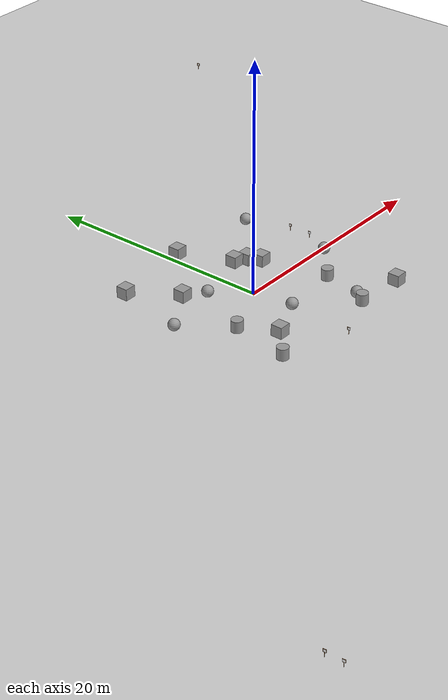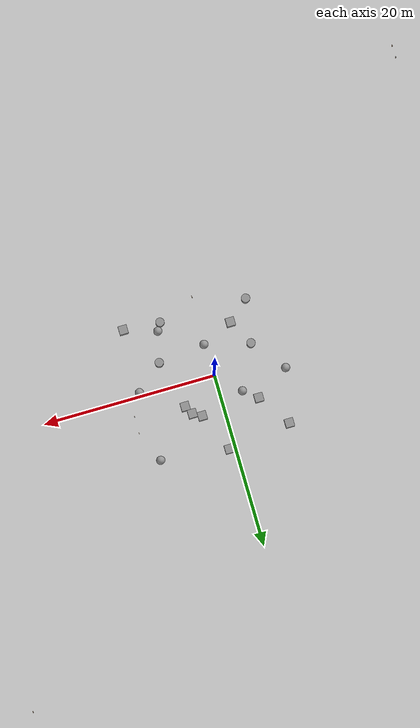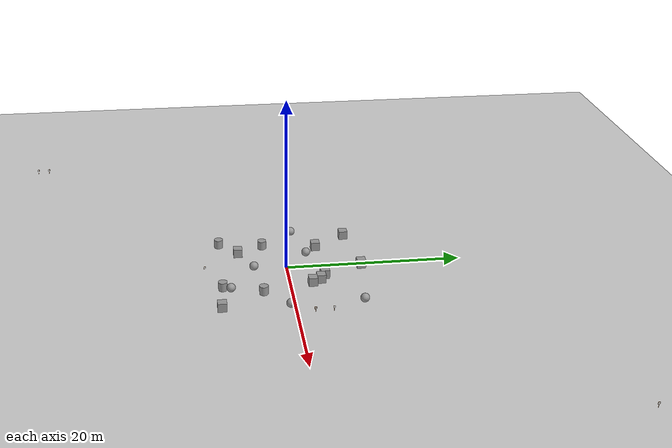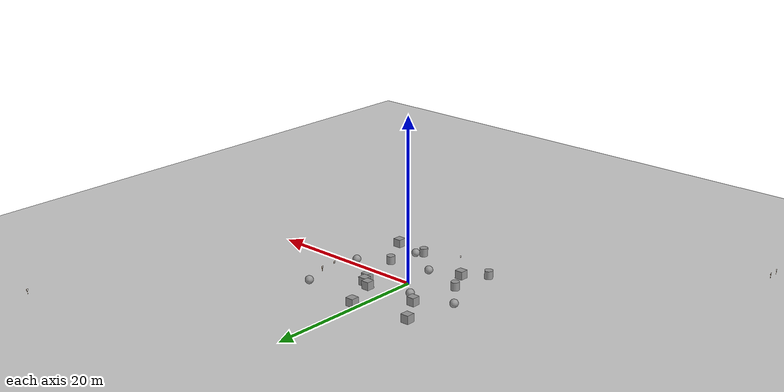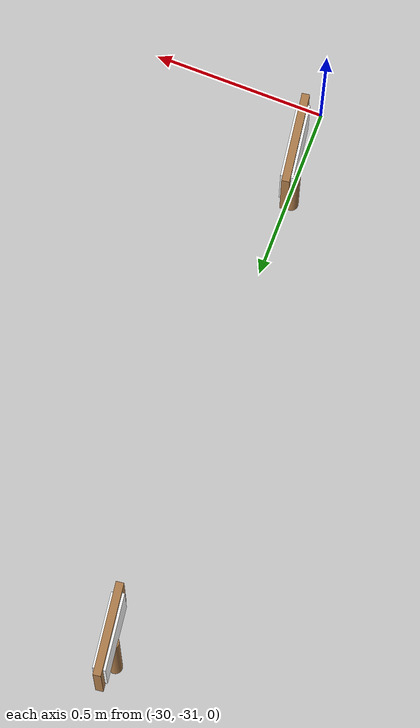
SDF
<sdf version="1.6">
 <world name="default">
  <light name="sun" type="directional">
   <pose>0 0 10 0 -0 0</pose>
   <diffuse>0.8 0.8 0.8 1</diffuse>
   <specular>0.2 0.2 0.2 1</specular>
   <attenuation>
    <range>1000</range>
    <constant>0.9</constant>
    <linear>0.01</linear>
    <quadratic>0.001</quadratic>
   </attenuation>
   <direction>-0.5 0.1 -0.9</direction>
  </light>
  <model name="ground_plane">
   <static>1</static>
   <link name="link">
    <collision name="collision">
     <geometry><plane><normal>0 0 1</normal><size>100 100</size></plane></geometry>
     <surface>
      <contact><collide_bitmask>65535</collide_bitmask></contact>
      <friction><ode><mu>100</mu><mu2>50</mu2></ode></friction>
     </surface>
    </collision>
    <visual name="visual">
     <cast_shadows>0</cast_shadows>
     <geometry><plane><normal>0 0 1</normal><size>100 100</size></plane></geometry>
     <material>
      <script><uri>file://media/materials/scripts/gazebo.material</uri><name>Gazebo/Grey</name></script>
     </material>
    </visual>
   </link>
  </model>
  <gravity>0 0 -9.8</gravity>
  <magnetic_field>6e-06 2.3e-05 -4.2e-05</magnetic_field>
  <atmosphere type="adiabatic"/>
  <physics name="default_physics" default="0" type="ode">
   <max_step_size>0.001</max_step_size>
   <real_time_factor>1</real_time_factor>
   <real_time_update_rate>1000</real_time_update_rate>
  </physics>
  <scene><ambient>0.4 0.4 0.4 1</ambient><background>0.7 0.7 0.7 1</background><shadows>1</shadows></scene>
  <audio><device>default</device></audio>
  <spherical_coordinates>
   <surface_model>EARTH_WGS84</surface_model>
   <latitude_deg>0</latitude_deg>
   <longitude_deg>0</longitude_deg>
   <elevation>0</elevation>
   <heading_deg>0</heading_deg>
  </spherical_coordinates>
  <model name="unit_box">
   <pose>-3.4049 -5.31639 0.499995 0 1e-05 -1.1e-05</pose>
   <link name="link">
    <inertial>
     <mass>1</mass>
     <inertia>
      <ixx>0.166667</ixx>
      <ixy>0</ixy>
      <ixz>0</ixz>
      <iyy>0.166667</iyy>
      <iyz>0</iyz>
      <izz>0.166667</izz>
     </inertia>
    </inertial>
    <collision name="collision"><geometry><box><size>1 1 1</size></box></geometry></collision>
    <visual name="visual">
     <geometry><box><size>1 1 1</size></box></geometry>
     <material>
      <script><name>Gazebo/Grey</name><uri>file://media/materials/scripts/gazebo.material</uri></script>
     </material>
    </visual>
   </link>
  </model>
  <model name="unit_box_0">
   <pose>-4.10124 3.81358 0.499995 0 1e-05 0</pose>
   <link name="link">
    <inertial>
     <mass>1</mass>
     <inertia>
      <ixx>0.166667</ixx>
      <ixy>0</ixy>
      <ixz>0</ixz>
      <iyy>0.166667</iyy>
      <iyz>0</iyz>
      <izz>0.166667</izz>
     </inertia>
    </inertial>
    <collision name="collision"><geometry><box><size>1 1 1</size></box></geometry></collision>
    <visual name="visual">
     <geometry><box><size>1 1 1</size></box></geometry>
     <material>
      <script><name>Gazebo/Grey</name><uri>file://media/materials/scripts/gazebo.material</uri></script>
     </material>
    </visual>
   </link>
  </model>
  <model name="unit_sphere">
   <pose>0.161192 -3.7282 0.5 0 -0 0</pose>
   <link name="link">
    <inertial>
     <mass>1</mass>
     <inertia><ixx>0.1</ixx><ixy>0</ixy><ixz>0</ixz><iyy>0.1</iyy><iyz>0</iyz><izz>0.1</izz></inertia>
    </inertial>
    <collision name="collision"><geometry><sphere><radius>0.5</radius></sphere></geometry></collision>
    <visual name="visual">
     <geometry><sphere><radius>0.5</radius></sphere></geometry>
     <material>
      <script><name>Gazebo/Grey</name><uri>file://media/materials/scripts/gazebo.material</uri></script>
     </material>
    </visual>
   </link>
  </model>
  <model name="unit_sphere_0">
   <pose>-2.55111 2.54212 0.5 0 -0 0</pose>
   <link name="link">
    <inertial>
     <mass>1</mass>
     <inertia><ixx>0.1</ixx><ixy>0</ixy><ixz>0</ixz><iyy>0.1</iyy><iyz>0</iyz><izz>0.1</izz></inertia>
    </inertial>
    <collision name="collision"><geometry><sphere><radius>0.5</radius></sphere></geometry></collision>
    <visual name="visual">
     <geometry><sphere><radius>0.5</radius></sphere></geometry>
     <material>
      <script><name>Gazebo/Grey</name><uri>file://media/materials/scripts/gazebo.material</uri></script>
     </material>
    </visual>
   </link>
  </model>
  <model name="unit_cylinder">
   <pose>4.24787 -7.48664 0.499999 0 0 -1.2e-05</pose>
   <link name="link">
    <inertial>
     <mass>1</mass>
     <inertia><ixx>0.145833</ixx><ixy>0</ixy><ixz>0</ixz><iyy>0.145833</iyy><iyz>0</iyz><izz>0.125</izz></inertia>
    </inertial>
    <collision name="collision">
     <geometry><cylinder><radius>0.5</radius><length>1</length></cylinder></geometry>
    </collision>
    <visual name="visual">
     <geometry><cylinder><radius>0.5</radius><length>1</length></cylinder></geometry>
     <material>
      <script><name>Gazebo/Grey</name><uri>file://media/materials/scripts/gazebo.material</uri></script>
     </material>
    </visual>
   </link>
  </model>
  <model name="unit_cylinder_1">
   <pose>5.59649 -3.0992 0.499998 3e-06 -3e-06 0</pose>
   <link name="link">
    <inertial>
     <mass>1</mass>
     <inertia><ixx>0.145833</ixx><ixy>0</ixy><ixz>0</ixz><iyy>0.145833</iyy><iyz>0</iyz><izz>0.125</izz></inertia>
    </inertial>
    <collision name="collision">
     <geometry><cylinder><radius>0.5</radius><length>1</length></cylinder></geometry>
    </collision>
    <visual name="visual">
     <geometry><cylinder><radius>0.5</radius><length>1</length></cylinder></geometry>
     <material>
      <script><name>Gazebo/Grey</name><uri>file://media/materials/scripts/gazebo.material</uri></script>
     </material>
    </visual>
   </link>
  </model>
  <model name="unit_box_1">
   <pose>2.59734 4.02787 0.499995 0 1e-05 0.007831</pose>
   <link name="link">
    <inertial>
     <mass>1</mass>
     <inertia>
      <ixx>0.166667</ixx>
      <ixy>0</ixy>
      <ixz>0</ixz>
      <iyy>0.166667</iyy>
      <iyz>0</iyz>
      <izz>0.166667</izz>
     </inertia>
    </inertial>
    <collision name="collision"><geometry><box><size>1 1 1</size></box></geometry></collision>
    <visual name="visual">
     <geometry><box><size>1 1 1</size></box></geometry>
     <material>
      <script><name>Gazebo/Grey</name><uri>file://media/materials/scripts/gazebo.material</uri></script>
     </material>
    </visual>
   </link>
  </model>
  <model name="unit_cylinder_2">
   <pose>-4.98063 -2.3723 0.499997 4e-06 4e-06 -0</pose>
   <link name="link">
    <inertial>
     <mass>1</mass>
     <inertia><ixx>0.145833</ixx><ixy>0</ixy><ixz>0</ixz><iyy>0.145833</iyy><iyz>0</iyz><izz>0.125</izz></inertia>
    </inertial>
    <collision name="collision">
     <geometry><cylinder><radius>0.5</radius><length>1</length></cylinder></geometry>
    </collision>
    <visual name="visual">
     <geometry><cylinder><radius>0.5</radius><length>1</length></cylinder></geometry>
     <material>
      <script><name>Gazebo/Grey</name><uri>file://media/materials/scripts/gazebo.material</uri></script>
     </material>
    </visual>
   </link>
  </model>
  <model name="unit_box_2">
   <pose>4.16233 2.47668 0.499995 -1e-05 -0 0.008036</pose>
   <link name="link">
    <inertial>
     <mass>1</mass>
     <inertia>
      <ixx>0.166667</ixx>
      <ixy>0</ixy>
      <ixz>0</ixz>
      <iyy>0.166667</iyy>
      <iyz>0</iyz>
      <izz>0.166667</izz>
     </inertia>
    </inertial>
    <collision name="collision"><geometry><box><size>1 1 1</size></box></geometry></collision>
    <visual name="visual">
     <geometry><box><size>1 1 1</size></box></geometry>
     <material>
      <script><name>Gazebo/Grey</name><uri>file://media/materials/scripts/gazebo.material</uri></script>
     </material>
    </visual>
   </link>
  </model>
  <model name="unit_sphere_2">
   <pose>4.75551 -6.6154 0.5 -0.014204 0.009421 0.00337</pose>
   <link name="link">
    <inertial>
     <mass>1</mass>
     <inertia><ixx>0.1</ixx><ixy>0</ixy><ixz>0</ixz><iyy>0.1</iyy><iyz>0</iyz><izz>0.1</izz></inertia>
    </inertial>
    <collision name="collision"><geometry><sphere><radius>0.5</radius></sphere></geometry></collision>
    <visual name="visual">
     <geometry><sphere><radius>0.5</radius></sphere></geometry>
     <material>
      <script><name>Gazebo/Grey</name><uri>file://media/materials/scripts/gazebo.material</uri></script>
     </material>
    </visual>
   </link>
  </model>
  <model name="unit_box_3">
   <pose>8.48757 -7.80084 0.499995 0 1e-05 -1.1e-05</pose>
   <link name="link">
    <inertial>
     <mass>1</mass>
     <inertia>
      <ixx>0.166667</ixx>
      <ixy>0</ixy>
      <ixz>0</ixz>
      <iyy>0.166667</iyy>
      <iyz>0</iyz>
      <izz>0.166667</izz>
     </inertia>
    </inertial>
    <collision name="collision"><geometry><box><size>1 1 1</size></box></geometry></collision>
    <visual name="visual">
     <geometry><box><size>1 1 1</size></box></geometry>
     <material>
      <script><name>Gazebo/Grey</name><uri>file://media/materials/scripts/gazebo.material</uri></script>
     </material>
    </visual>
   </link>
  </model>
  <model name="unit_box_4">
   <pose>-6.61088 7.51602 0.499995 0 1e-05 0</pose>
   <link name="link">
    <inertial>
     <mass>1</mass>
     <inertia>
      <ixx>0.166667</ixx>
      <ixy>0</ixy>
      <ixz>0</ixz>
      <iyy>0.166667</iyy>
      <iyz>0</iyz>
      <izz>0.166667</izz>
     </inertia>
    </inertial>
    <collision name="collision"><geometry><box><size>1 1 1</size></box></geometry></collision>
    <visual name="visual">
     <geometry><box><size>1 1 1</size></box></geometry>
     <material>
      <script><name>Gazebo/Grey</name><uri>file://media/materials/scripts/gazebo.material</uri></script>
     </material>
    </visual>
   </link>
  </model>
  <model name="unit_cylinder_3">
   <pose>-5.81047 -7.41812 0.499999 0 -0 0</pose>
   <link name="link">
    <inertial>
     <mass>1</mass>
     <inertia><ixx>0.145833</ixx><ixy>0</ixy><ixz>0</ixz><iyy>0.145833</iyy><iyz>0</iyz><izz>0.125</izz></inertia>
    </inertial>
    <collision name="collision">
     <geometry><cylinder><radius>0.5</radius><length>1</length></cylinder></geometry>
    </collision>
    <visual name="visual">
     <geometry><cylinder><radius>0.5</radius><length>1</length></cylinder></geometry>
     <material>
      <script><name>Gazebo/Grey</name><uri>file://media/materials/scripts/gazebo.material</uri></script>
     </material>
    </visual>
   </link>
  </model>
  <model name="unit_sphere_3">
   <pose>8.48345 7.53587 0.5 0 -0 0</pose>
   <link name="link">
    <inertial>
     <mass>1</mass>
     <inertia><ixx>0.1</ixx><ixy>0</ixy><ixz>0</ixz><iyy>0.1</iyy><iyz>0</iyz><izz>0.1</izz></inertia>
    </inertial>
    <collision name="collision"><geometry><sphere><radius>0.5</radius></sphere></geometry></collision>
    <visual name="visual">
     <geometry><sphere><radius>0.5</radius></sphere></geometry>
     <material>
      <script><name>Gazebo/Grey</name><uri>file://media/materials/scripts/gazebo.material</uri></script>
     </material>
    </visual>
   </link>
  </model>
  <model name="unit_box_5">
   <pose>0.717745 8.45941 0.499995 0 1e-05 -1.1e-05</pose>
   <link name="link">
    <inertial>
     <mass>1</mass>
     <inertia>
      <ixx>0.166667</ixx>
      <ixy>0</ixy>
      <ixz>0</ixz>
      <iyy>0.166667</iyy>
      <iyz>0</iyz>
      <izz>0.166667</izz>
     </inertia>
    </inertial>
    <collision name="collision"><geometry><box><size>1 1 1</size></box></geometry></collision>
    <visual name="visual">
     <geometry><box><size>1 1 1</size></box></geometry>
     <material>
      <script><name>Gazebo/Grey</name><uri>file://media/materials/scripts/gazebo.material</uri></script>
     </material>
    </visual>
   </link>
  </model>
  <model name="unit_sphere_4">
   <pose>8.67849 -0.485052 0.5 0 -0 0</pose>
   <link name="link">
    <inertial>
     <mass>1</mass>
     <inertia><ixx>0.1</ixx><ixy>0</ixy><ixz>0</ixz><iyy>0.1</iyy><iyz>0</iyz><izz>0.1</izz></inertia>
    </inertial>
    <collision name="collision"><geometry><sphere><radius>0.5</radius></sphere></geometry></collision>
    <visual name="visual">
     <geometry><sphere><radius>0.5</radius></sphere></geometry>
     <material>
      <script><name>Gazebo/Grey</name><uri>file://media/materials/scripts/gazebo.material</uri></script>
     </material>
    </visual>
   </link>
  </model>
  <model name="unit_box_6">
   <pose>3.60177 3.47234 0.499995 0 -1e-05 0.007921</pose>
   <link name="link">
    <inertial>
     <mass>1</mass>
     <inertia>
      <ixx>0.166667</ixx>
      <ixy>0</ixy>
      <ixz>0</ixz>
      <iyy>0.166667</iyy>
      <iyz>0</iyz>
      <izz>0.166667</izz>
     </inertia>
    </inertial>
    <collision name="collision"><geometry><box><size>1 1 1</size></box></geometry></collision>
    <visual name="visual">
     <geometry><box><size>1 1 1</size></box></geometry>
     <material>
      <script><name>Gazebo/Grey</name><uri>file://media/materials/scripts/gazebo.material</uri></script>
     </material>
    </visual>
   </link>
  </model>
  <model name="unit_sphere_1">
   <pose>-7.97349 1.37373 0.5 0 -0 0</pose>
   <link name="link">
    <inertial>
     <mass>1</mass>
     <inertia><ixx>0.1</ixx><ixy>0</ixy><ixz>0</ixz><iyy>0.1</iyy><iyz>0</iyz><izz>0.1</izz></inertia>
    </inertial>
    <collision name="collision"><geometry><sphere><radius>0.5</radius></sphere></geometry></collision>
    <visual name="visual">
     <geometry><sphere><radius>0.5</radius></sphere></geometry>
     <material>
      <script><name>Gazebo/Grey</name><uri>file://media/materials/scripts/gazebo.material</uri></script>
     </material>
    </visual>
   </link>
  </model>
  <model name="aruco_wood_thin">
   <link name="link_0">
    <inertial>
     <mass>1</mass>
     <inertia><ixx>0.145833</ixx><ixy>0</ixy><ixz>0</ixz><iyy>0.145833</iyy><iyz>0</iyz><izz>0.125</izz></inertia>
    </inertial>
    <pose>-0.017932 0.660168 -0.097628 0 -0 0</pose>
    <visual name="visual">
     <geometry><cylinder><radius>0.02</radius><length>0.4</length></cylinder></geometry>
     <material>
      <lighting>1</lighting>
      <script><uri>file://media/materials/scripts/gazebo.material</uri><name>Gazebo/Wood</name></script>
      <shader type="vertex"><normal_map>__default__</normal_map></shader>
      <ambient>0.3 0.3 0.3 1</ambient>
      <diffuse>0.7 0.7 0.7 1</diffuse>
      <specular>0.01 0.01 0.01 1</specular>
      <emissive>0 0 0 1</emissive>
     </material>
    </visual>
    <collision name="collision">
     <geometry><cylinder><radius>0.02</radius><length>0.4</length></cylinder></geometry>
     <surface>
      <friction>
       <ode><mu>1</mu><mu2>1</mu2><fdir1>0 0 0</fdir1><slip1>0</slip1><slip2>0</slip2></ode>
       <torsional>
        <coefficient>1</coefficient>
        <patch_radius>0</patch_radius>
        <surface_radius>0</surface_radius>
        <use_patch_radius>1</use_patch_radius>
        <ode><slip>0</slip></ode>
       </torsional>
      </friction>
      <bounce><restitution_coefficient>0</restitution_coefficient><threshold>1e+06</threshold></bounce>
      <contact>
       <collide_without_contact>0</collide_without_contact>
       <collide_without_contact_bitmask>1</collide_without_contact_bitmask>
       <collide_bitmask>1</collide_bitmask>
       <ode>
        <soft_cfm>0</soft_cfm>
        <soft_erp>0.2</soft_erp>
        <kp>1e+13</kp>
        <kd>1</kd>
        <max_vel>0.01</max_vel>
        <min_depth>0</min_depth>
       </ode>
       <bullet>
        <split_impulse>1</split_impulse>
        <split_impulse_penetration_threshold>-0.01</split_impulse_penetration_threshold>
        <soft_cfm>0</soft_cfm>
        <soft_erp>0.2</soft_erp>
        <kp>1e+13</kp>
        <kd>1</kd>
       </bullet>
      </contact>
     </surface>
    </collision>
   </link>
   <link name="link_1">
    <inertial>
     <mass>1.21407</mass>
     <inertia>
      <ixx>0.00864359</ixx>
      <ixy>0</ixy>
      <ixz>0</ixz>
      <iyy>0.00421539</iyy>
      <iyz>0</iyz>
      <izz>0.00446773</izz>
     </inertia>
    </inertial>
    <pose>-0.025899 0.66382 0.194379 0 -0 0</pose>
    <visual name="visual">
     <geometry><box><size>0.013978 0.209676 0.203642</size></box></geometry>
     <material>
      <script><uri>file://scripts</uri><uri>file://textures</uri><name>aruco/standard_opp</name></script>
      <emissive>0 0 0 1</emissive>
      <shader type="vertex"><normal_map>__default__</normal_map></shader>
      <ambient>1 1 1 1</ambient>
      <diffuse>1 1 1 1</diffuse>
      <specular>0 0 0 1</specular>
     </material>
    </visual>
    <collision name="collision">
     <geometry><box><size>0.013978 0.209676 0.203642</size></box></geometry>
     <surface>
      <friction>
       <ode><mu>1</mu><mu2>1</mu2><fdir1>0 0 0</fdir1><slip1>0</slip1><slip2>0</slip2></ode>
       <torsional>
        <coefficient>1</coefficient>
        <patch_radius>0</patch_radius>
        <surface_radius>0</surface_radius>
        <use_patch_radius>1</use_patch_radius>
        <ode><slip>0</slip></ode>
       </torsional>
      </friction>
      <bounce><restitution_coefficient>0</restitution_coefficient><threshold>1e+06</threshold></bounce>
      <contact>
       <collide_without_contact>0</collide_without_contact>
       <collide_without_contact_bitmask>1</collide_without_contact_bitmask>
       <collide_bitmask>1</collide_bitmask>
       <ode>
        <soft_cfm>0</soft_cfm>
        <soft_erp>0.2</soft_erp>
        <kp>1e+13</kp>
        <kd>1</kd>
        <max_vel>0.01</max_vel>
        <min_depth>0</min_depth>
       </ode>
       <bullet>
        <split_impulse>1</split_impulse>
        <split_impulse_penetration_threshold>-0.01</split_impulse_penetration_threshold>
        <soft_cfm>0</soft_cfm>
        <soft_erp>0.2</soft_erp>
        <kp>1e+13</kp>
        <kd>1</kd>
       </bullet>
      </contact>
     </surface>
    </collision>
   </link>
   <link name="link_1_clone">
    <inertial>
     <mass>0.519809</mass>
     <inertia>
      <ixx>0.00549167</ixx>
      <ixy>0</ixy>
      <ixz>0</ixz>
      <iyy>0.00278045</iyy>
      <iyz>0</iyz>
      <izz>0.00275135</izz>
     </inertia>
    </inertial>
    <pose>-0.015207 0.663184 0.195267 0 -0 0</pose>
    <visual name="visual">
     <geometry><box><size>0.021523 0.251103 0.252437</size></box></geometry>
     <material>
      <script><uri>file://scripts</uri><uri>file://textures</uri><name>Gazebo/Wood</name></script>
      <shader type="vertex"><normal_map>__default__</normal_map></shader>
      <ambient>1 1 1 1</ambient>
      <diffuse>1 1 1 1</diffuse>
      <specular>0 0 0 1</specular>
      <emissive>0 0 0 1</emissive>
     </material>
    </visual>
    <collision name="collision">
     <geometry><box><size>0.021523 0.251103 0.252437</size></box></geometry>
     <surface>
      <friction>
       <ode><mu>1</mu><mu2>1</mu2><fdir1>0 0 0</fdir1><slip1>0</slip1><slip2>0</slip2></ode>
       <torsional>
        <coefficient>1</coefficient>
        <patch_radius>0</patch_radius>
        <surface_radius>0</surface_radius>
        <use_patch_radius>1</use_patch_radius>
        <ode><slip>0</slip></ode>
       </torsional>
      </friction>
      <bounce><restitution_coefficient>0</restitution_coefficient><threshold>1e+06</threshold></bounce>
      <contact>
       <collide_without_contact>0</collide_without_contact>
       <collide_without_contact_bitmask>1</collide_without_contact_bitmask>
       <collide_bitmask>1</collide_bitmask>
       <ode>
        <soft_cfm>0</soft_cfm>
        <soft_erp>0.2</soft_erp>
        <kp>1e+13</kp>
        <kd>1</kd>
        <max_vel>0.01</max_vel>
        <min_depth>0</min_depth>
       </ode>
       <bullet>
        <split_impulse>1</split_impulse>
        <split_impulse_penetration_threshold>-0.01</split_impulse_penetration_threshold>
        <soft_cfm>0</soft_cfm>
        <soft_erp>0.2</soft_erp>
        <kp>1e+13</kp>
        <kd>1</kd>
       </bullet>
      </contact>
     </surface>
    </collision>
   </link>
   <link name="link_1_clone_0">
    <inertial>
     <mass>0.238009</mass>
     <inertia>
      <ixx>0.00161175</ixx>
      <ixy>0</ixy>
      <ixz>0</ixz>
      <iyy>0.000787067</iyy>
      <iyz>0</iyz>
      <izz>0.000832042</izz>
     </inertia>
    </inertial>
    <pose>-0.00403 0.665261 0.195247 0 -0 0</pose>
    <visual name="visual">
     <geometry><box><size>0.013624 0.204363 0.198738</size></box></geometry>
     <material>
      <script><uri>file://scripts</uri><uri>file://textures</uri><name>aruco/standard_opp</name></script>
      <emissive>0 0 0 1</emissive>
      <shader type="vertex"><normal_map>__default__</normal_map></shader>
      <ambient>1 1 1 1</ambient>
      <diffuse>1 1 1 1</diffuse>
      <specular>0 0 0 1</specular>
     </material>
    </visual>
    <collision name="collision">
     <geometry><box><size>0.013624 0.204363 0.198738</size></box></geometry>
     <surface>
      <friction>
       <ode><mu>1</mu><mu2>1</mu2><fdir1>0 0 0</fdir1><slip1>0</slip1><slip2>0</slip2></ode>
       <torsional>
        <coefficient>1</coefficient>
        <patch_radius>0</patch_radius>
        <surface_radius>0</surface_radius>
        <use_patch_radius>1</use_patch_radius>
        <ode><slip>0</slip></ode>
       </torsional>
      </friction>
      <bounce><restitution_coefficient>0</restitution_coefficient><threshold>1e+06</threshold></bounce>
      <contact>
       <collide_without_contact>0</collide_without_contact>
       <collide_without_contact_bitmask>1</collide_without_contact_bitmask>
       <collide_bitmask>1</collide_bitmask>
       <ode>
        <soft_cfm>0</soft_cfm>
        <soft_erp>0.2</soft_erp>
        <kp>1e+13</kp>
        <kd>1</kd>
        <max_vel>0.01</max_vel>
        <min_depth>0</min_depth>
       </ode>
       <bullet>
        <split_impulse>1</split_impulse>
        <split_impulse_penetration_threshold>-0.01</split_impulse_penetration_threshold>
        <soft_cfm>0</soft_cfm>
        <soft_erp>0.2</soft_erp>
        <kp>1e+13</kp>
        <kd>1</kd>
       </bullet>
      </contact>
     </surface>
    </collision>
   </link>
   <joint name="link_0_JOINT_0" type="fixed">
    <parent>link_0</parent>
    <child>link_1</child>
    <physics>
     <ode><limit><cfm>0</cfm><erp>0.2</erp></limit><suspension><cfm>0</cfm><erp>0.2</erp></suspension></ode>
    </physics>
   </joint>
   <joint name="link_1_JOINT_0_0" type="fixed">
    <parent>link_1</parent>
    <child>link_1_clone_0</child>
    <physics>
     <ode><limit><cfm>0</cfm><erp>0.2</erp></limit><suspension><cfm>0</cfm><erp>0.2</erp></suspension></ode>
    </physics>
   </joint>
   <joint name="link_1_JOINT_0" type="fixed">
    <parent>link_1</parent>
    <child>link_1_clone</child>
    <physics>
     <ode><limit><cfm>0</cfm><erp>0.2</erp></limit><suspension><cfm>0</cfm><erp>0.2</erp></suspension></ode>
    </physics>
   </joint>
   <static>0</static>
   <pose>0.075916 -9.96004 0.297635 -1e-05 -3e-06 0.139574</pose>
  </model>
  <model name="aruco_wood_thin_0">
   <link name="link_0">
    <inertial>
     <mass>1</mass>
     <inertia><ixx>0.145833</ixx><ixy>0</ixy><ixz>0</ixz><iyy>0.145833</iyy><iyz>0</iyz><izz>0.125</izz></inertia>
    </inertial>
    <pose>-0.017932 0.660168 -0.097628 0 -0 0</pose>
    <visual name="visual">
     <geometry><cylinder><radius>0.02</radius><length>0.4</length></cylinder></geometry>
     <material>
      <lighting>1</lighting>
      <script><uri>file://media/materials/scripts/gazebo.material</uri><name>Gazebo/Wood</name></script>
      <shader type="vertex"><normal_map>__default__</normal_map></shader>
      <ambient>0.3 0.3 0.3 1</ambient>
      <diffuse>0.7 0.7 0.7 1</diffuse>
      <specular>0.01 0.01 0.01 1</specular>
      <emissive>0 0 0 1</emissive>
     </material>
    </visual>
    <collision name="collision">
     <geometry><cylinder><radius>0.02</radius><length>0.4</length></cylinder></geometry>
     <surface>
      <friction>
       <ode><mu>1</mu><mu2>1</mu2><fdir1>0 0 0</fdir1><slip1>0</slip1><slip2>0</slip2></ode>
       <torsional>
        <coefficient>1</coefficient>
        <patch_radius>0</patch_radius>
        <surface_radius>0</surface_radius>
        <use_patch_radius>1</use_patch_radius>
        <ode><slip>0</slip></ode>
       </torsional>
      </friction>
      <bounce><restitution_coefficient>0</restitution_coefficient><threshold>1e+06</threshold></bounce>
      <contact>
       <collide_without_contact>0</collide_without_contact>
       <collide_without_contact_bitmask>1</collide_without_contact_bitmask>
       <collide_bitmask>1</collide_bitmask>
       <ode>
        <soft_cfm>0</soft_cfm>
        <soft_erp>0.2</soft_erp>
        <kp>1e+13</kp>
        <kd>1</kd>
        <max_vel>0.01</max_vel>
        <min_depth>0</min_depth>
       </ode>
       <bullet>
        <split_impulse>1</split_impulse>
        <split_impulse_penetration_threshold>-0.01</split_impulse_penetration_threshold>
        <soft_cfm>0</soft_cfm>
        <soft_erp>0.2</soft_erp>
        <kp>1e+13</kp>
        <kd>1</kd>
       </bullet>
      </contact>
     </surface>
    </collision>
   </link>
   <link name="link_1">
    <inertial>
     <mass>1.21407</mass>
     <inertia>
      <ixx>0.00864359</ixx>
      <ixy>0</ixy>
      <ixz>0</ixz>
      <iyy>0.00421539</iyy>
      <iyz>0</iyz>
      <izz>0.00446773</izz>
     </inertia>
    </inertial>
    <pose>-0.025899 0.66382 0.194379 0 -0 0</pose>
    <visual name="visual">
     <geometry><box><size>0.013978 0.209676 0.203642</size></box></geometry>
     <material>
      <script><uri>file://scripts</uri><uri>file://textures</uri><name>aruco/standard_opp</name></script>
      <emissive>0 0 0 1</emissive>
      <shader type="vertex"><normal_map>__default__</normal_map></shader>
      <ambient>1 1 1 1</ambient>
      <diffuse>1 1 1 1</diffuse>
      <specular>0 0 0 1</specular>
     </material>
    </visual>
    <collision name="collision">
     <geometry><box><size>0.013978 0.209676 0.203642</size></box></geometry>
     <surface>
      <friction>
       <ode><mu>1</mu><mu2>1</mu2><fdir1>0 0 0</fdir1><slip1>0</slip1><slip2>0</slip2></ode>
       <torsional>
        <coefficient>1</coefficient>
        <patch_radius>0</patch_radius>
        <surface_radius>0</surface_radius>
        <use_patch_radius>1</use_patch_radius>
        <ode><slip>0</slip></ode>
       </torsional>
      </friction>
      <bounce><restitution_coefficient>0</restitution_coefficient><threshold>1e+06</threshold></bounce>
      <contact>
       <collide_without_contact>0</collide_without_contact>
       <collide_without_contact_bitmask>1</collide_without_contact_bitmask>
       <collide_bitmask>1</collide_bitmask>
       <ode>
        <soft_cfm>0</soft_cfm>
        <soft_erp>0.2</soft_erp>
        <kp>1e+13</kp>
        <kd>1</kd>
        <max_vel>0.01</max_vel>
        <min_depth>0</min_depth>
       </ode>
       <bullet>
        <split_impulse>1</split_impulse>
        <split_impulse_penetration_threshold>-0.01</split_impulse_penetration_threshold>
        <soft_cfm>0</soft_cfm>
        <soft_erp>0.2</soft_erp>
        <kp>1e+13</kp>
        <kd>1</kd>
       </bullet>
      </contact>
     </surface>
    </collision>
   </link>
   <link name="link_1_clone">
    <inertial>
     <mass>0.519809</mass>
     <inertia>
      <ixx>0.00549167</ixx>
      <ixy>0</ixy>
      <ixz>0</ixz>
      <iyy>0.00278045</iyy>
      <iyz>0</iyz>
      <izz>0.00275135</izz>
     </inertia>
    </inertial>
    <pose>-0.015207 0.663184 0.195267 0 -0 0</pose>
    <visual name="visual">
     <geometry><box><size>0.021523 0.251103 0.252437</size></box></geometry>
     <material>
      <script><uri>file://scripts</uri><uri>file://textures</uri><name>Gazebo/Wood</name></script>
      <shader type="vertex"><normal_map>__default__</normal_map></shader>
      <ambient>1 1 1 1</ambient>
      <diffuse>1 1 1 1</diffuse>
      <specular>0 0 0 1</specular>
      <emissive>0 0 0 1</emissive>
     </material>
    </visual>
    <collision name="collision">
     <geometry><box><size>0.021523 0.251103 0.252437</size></box></geometry>
     <surface>
      <friction>
       <ode><mu>1</mu><mu2>1</mu2><fdir1>0 0 0</fdir1><slip1>0</slip1><slip2>0</slip2></ode>
       <torsional>
        <coefficient>1</coefficient>
        <patch_radius>0</patch_radius>
        <surface_radius>0</surface_radius>
        <use_patch_radius>1</use_patch_radius>
        <ode><slip>0</slip></ode>
       </torsional>
      </friction>
      <bounce><restitution_coefficient>0</restitution_coefficient><threshold>1e+06</threshold></bounce>
      <contact>
       <collide_without_contact>0</collide_without_contact>
       <collide_without_contact_bitmask>1</collide_without_contact_bitmask>
       <collide_bitmask>1</collide_bitmask>
       <ode>
        <soft_cfm>0</soft_cfm>
        <soft_erp>0.2</soft_erp>
        <kp>1e+13</kp>
        <kd>1</kd>
        <max_vel>0.01</max_vel>
        <min_depth>0</min_depth>
       </ode>
       <bullet>
        <split_impulse>1</split_impulse>
        <split_impulse_penetration_threshold>-0.01</split_impulse_penetration_threshold>
        <soft_cfm>0</soft_cfm>
        <soft_erp>0.2</soft_erp>
        <kp>1e+13</kp>
        <kd>1</kd>
       </bullet>
      </contact>
     </surface>
    </collision>
   </link>
   <link name="link_1_clone_0">
    <inertial>
     <mass>0.238009</mass>
     <inertia>
      <ixx>0.00161175</ixx>
      <ixy>0</ixy>
      <ixz>0</ixz>
      <iyy>0.000787067</iyy>
      <iyz>0</iyz>
      <izz>0.000832042</izz>
     </inertia>
    </inertial>
    <pose>-0.00403 0.665261 0.195247 0 -0 0</pose>
    <visual name="visual">
     <geometry><box><size>0.013624 0.204363 0.198738</size></box></geometry>
     <material>
      <script><uri>file://scripts</uri><uri>file://textures</uri><name>aruco/standard_opp</name></script>
      <emissive>0 0 0 1</emissive>
      <shader type="vertex"><normal_map>__default__</normal_map></shader>
      <ambient>1 1 1 1</ambient>
      <diffuse>1 1 1 1</diffuse>
      <specular>0 0 0 1</specular>
     </material>
    </visual>
    <collision name="collision">
     <geometry><box><size>0.013624 0.204363 0.198738</size></box></geometry>
     <surface>
      <friction>
       <ode><mu>1</mu><mu2>1</mu2><fdir1>0 0 0</fdir1><slip1>0</slip1><slip2>0</slip2></ode>
       <torsional>
        <coefficient>1</coefficient>
        <patch_radius>0</patch_radius>
        <surface_radius>0</surface_radius>
        <use_patch_radius>1</use_patch_radius>
        <ode><slip>0</slip></ode>
       </torsional>
      </friction>
      <bounce><restitution_coefficient>0</restitution_coefficient><threshold>1e+06</threshold></bounce>
      <contact>
       <collide_without_contact>0</collide_without_contact>
       <collide_without_contact_bitmask>1</collide_without_contact_bitmask>
       <collide_bitmask>1</collide_bitmask>
       <ode>
        <soft_cfm>0</soft_cfm>
        <soft_erp>0.2</soft_erp>
        <kp>1e+13</kp>
        <kd>1</kd>
        <max_vel>0.01</max_vel>
        <min_depth>0</min_depth>
       </ode>
       <bullet>
        <split_impulse>1</split_impulse>
        <split_impulse_penetration_threshold>-0.01</split_impulse_penetration_threshold>
        <soft_cfm>0</soft_cfm>
        <soft_erp>0.2</soft_erp>
        <kp>1e+13</kp>
        <kd>1</kd>
       </bullet>
      </contact>
     </surface>
    </collision>
   </link>
   <joint name="link_0_JOINT_0" type="fixed">
    <parent>link_0</parent>
    <child>link_1</child>
    <physics>
     <ode><limit><cfm>0</cfm><erp>0.2</erp></limit><suspension><cfm>0</cfm><erp>0.2</erp></suspension></ode>
    </physics>
   </joint>
   <joint name="link_1_JOINT_0_0" type="fixed">
    <parent>link_1</parent>
    <child>link_1_clone_0</child>
    <physics>
     <ode><limit><cfm>0</cfm><erp>0.2</erp></limit><suspension><cfm>0</cfm><erp>0.2</erp></suspension></ode>
    </physics>
   </joint>
   <joint name="link_1_JOINT_0" type="fixed">
    <parent>link_1</parent>
    <child>link_1_clone</child>
    <physics>
     <ode><limit><cfm>0</cfm><erp>0.2</erp></limit><suspension><cfm>0</cfm><erp>0.2</erp></suspension></ode>
    </physics>
   </joint>
   <static>0</static>
   <pose>30.0765 30.0395 0.297612 1.1e-05 2.5e-05 0.13091</pose>
  </model>
  <model name="aruco_wood_thin_1">
   <link name="link_0">
    <inertial>
     <mass>1</mass>
     <inertia><ixx>0.145833</ixx><ixy>0</ixy><ixz>0</ixz><iyy>0.145833</iyy><iyz>0</iyz><izz>0.125</izz></inertia>
    </inertial>
    <pose>-0.017932 0.660168 -0.097628 0 -0 0</pose>
    <visual name="visual">
     <geometry><cylinder><radius>0.02</radius><length>0.4</length></cylinder></geometry>
     <material>
      <lighting>1</lighting>
      <script><uri>file://media/materials/scripts/gazebo.material</uri><name>Gazebo/Wood</name></script>
      <shader type="vertex"><normal_map>__default__</normal_map></shader>
      <ambient>0.3 0.3 0.3 1</ambient>
      <diffuse>0.7 0.7 0.7 1</diffuse>
      <specular>0.01 0.01 0.01 1</specular>
      <emissive>0 0 0 1</emissive>
     </material>
    </visual>
    <collision name="collision">
     <geometry><cylinder><radius>0.02</radius><length>0.4</length></cylinder></geometry>
     <surface>
      <friction>
       <ode><mu>1</mu><mu2>1</mu2><fdir1>0 0 0</fdir1><slip1>0</slip1><slip2>0</slip2></ode>
       <torsional>
        <coefficient>1</coefficient>
        <patch_radius>0</patch_radius>
        <surface_radius>0</surface_radius>
        <use_patch_radius>1</use_patch_radius>
        <ode><slip>0</slip></ode>
       </torsional>
      </friction>
      <bounce><restitution_coefficient>0</restitution_coefficient><threshold>1e+06</threshold></bounce>
      <contact>
       <collide_without_contact>0</collide_without_contact>
       <collide_without_contact_bitmask>1</collide_without_contact_bitmask>
       <collide_bitmask>1</collide_bitmask>
       <ode>
        <soft_cfm>0</soft_cfm>
        <soft_erp>0.2</soft_erp>
        <kp>1e+13</kp>
        <kd>1</kd>
        <max_vel>0.01</max_vel>
        <min_depth>0</min_depth>
       </ode>
       <bullet>
        <split_impulse>1</split_impulse>
        <split_impulse_penetration_threshold>-0.01</split_impulse_penetration_threshold>
        <soft_cfm>0</soft_cfm>
        <soft_erp>0.2</soft_erp>
        <kp>1e+13</kp>
        <kd>1</kd>
       </bullet>
      </contact>
     </surface>
    </collision>
   </link>
   <link name="link_1">
    <inertial>
     <mass>1.21407</mass>
     <inertia>
      <ixx>0.00864359</ixx>
      <ixy>0</ixy>
      <ixz>0</ixz>
      <iyy>0.00421539</iyy>
      <iyz>0</iyz>
      <izz>0.00446773</izz>
     </inertia>
    </inertial>
    <pose>-0.025899 0.66382 0.194379 0 -0 0</pose>
    <visual name="visual">
     <geometry><box><size>0.013978 0.209676 0.203642</size></box></geometry>
     <material>
      <script><uri>file://scripts</uri><uri>file://textures</uri><name>aruco/standard_opp</name></script>
      <emissive>0 0 0 1</emissive>
      <shader type="vertex"><normal_map>__default__</normal_map></shader>
      <ambient>1 1 1 1</ambient>
      <diffuse>1 1 1 1</diffuse>
      <specular>0 0 0 1</specular>
     </material>
    </visual>
    <collision name="collision">
     <geometry><box><size>0.013978 0.209676 0.203642</size></box></geometry>
     <surface>
      <friction>
       <ode><mu>1</mu><mu2>1</mu2><fdir1>0 0 0</fdir1><slip1>0</slip1><slip2>0</slip2></ode>
       <torsional>
        <coefficient>1</coefficient>
        <patch_radius>0</patch_radius>
        <surface_radius>0</surface_radius>
        <use_patch_radius>1</use_patch_radius>
        <ode><slip>0</slip></ode>
       </torsional>
      </friction>
      <bounce><restitution_coefficient>0</restitution_coefficient><threshold>1e+06</threshold></bounce>
      <contact>
       <collide_without_contact>0</collide_without_contact>
       <collide_without_contact_bitmask>1</collide_without_contact_bitmask>
       <collide_bitmask>1</collide_bitmask>
       <ode>
        <soft_cfm>0</soft_cfm>
        <soft_erp>0.2</soft_erp>
        <kp>1e+13</kp>
        <kd>1</kd>
        <max_vel>0.01</max_vel>
        <min_depth>0</min_depth>
       </ode>
       <bullet>
        <split_impulse>1</split_impulse>
        <split_impulse_penetration_threshold>-0.01</split_impulse_penetration_threshold>
        <soft_cfm>0</soft_cfm>
        <soft_erp>0.2</soft_erp>
        <kp>1e+13</kp>
        <kd>1</kd>
       </bullet>
      </contact>
     </surface>
    </collision>
   </link>
   <link name="link_1_clone">
    <inertial>
     <mass>0.519809</mass>
     <inertia>
      <ixx>0.00549167</ixx>
      <ixy>0</ixy>
      <ixz>0</ixz>
      <iyy>0.00278045</iyy>
      <iyz>0</iyz>
      <izz>0.00275135</izz>
     </inertia>
    </inertial>
    <pose>-0.015207 0.663184 0.195267 0 -0 0</pose>
    <visual name="visual">
     <geometry><box><size>0.021523 0.251103 0.252437</size></box></geometry>
     <material>
      <script><uri>file://scripts</uri><uri>file://textures</uri><name>Gazebo/Wood</name></script>
      <shader type="vertex"><normal_map>__default__</normal_map></shader>
      <ambient>1 1 1 1</ambient>
      <diffuse>1 1 1 1</diffuse>
      <specular>0 0 0 1</specular>
      <emissive>0 0 0 1</emissive>
     </material>
    </visual>
    <collision name="collision">
     <geometry><box><size>0.021523 0.251103 0.252437</size></box></geometry>
     <surface>
      <friction>
       <ode><mu>1</mu><mu2>1</mu2><fdir1>0 0 0</fdir1><slip1>0</slip1><slip2>0</slip2></ode>
       <torsional>
        <coefficient>1</coefficient>
        <patch_radius>0</patch_radius>
        <surface_radius>0</surface_radius>
        <use_patch_radius>1</use_patch_radius>
        <ode><slip>0</slip></ode>
       </torsional>
      </friction>
      <bounce><restitution_coefficient>0</restitution_coefficient><threshold>1e+06</threshold></bounce>
      <contact>
       <collide_without_contact>0</collide_without_contact>
       <collide_without_contact_bitmask>1</collide_without_contact_bitmask>
       <collide_bitmask>1</collide_bitmask>
       <ode>
        <soft_cfm>0</soft_cfm>
        <soft_erp>0.2</soft_erp>
        <kp>1e+13</kp>
        <kd>1</kd>
        <max_vel>0.01</max_vel>
        <min_depth>0</min_depth>
       </ode>
       <bullet>
        <split_impulse>1</split_impulse>
        <split_impulse_penetration_threshold>-0.01</split_impulse_penetration_threshold>
        <soft_cfm>0</soft_cfm>
        <soft_erp>0.2</soft_erp>
        <kp>1e+13</kp>
        <kd>1</kd>
       </bullet>
      </contact>
     </surface>
    </collision>
   </link>
   <link name="link_1_clone_0">
    <inertial>
     <mass>0.238009</mass>
     <inertia>
      <ixx>0.00161175</ixx>
      <ixy>0</ixy>
      <ixz>0</ixz>
      <iyy>0.000787067</iyy>
      <iyz>0</iyz>
      <izz>0.000832042</izz>
     </inertia>
    </inertial>
    <pose>-0.00403 0.665261 0.195247 0 -0 0</pose>
    <visual name="visual">
     <geometry><box><size>0.013624 0.204363 0.198738</size></box></geometry>
     <material>
      <script><uri>file://scripts</uri><uri>file://textures</uri><name>aruco/standard_opp</name></script>
      <emissive>0 0 0 1</emissive>
      <shader type="vertex"><normal_map>__default__</normal_map></shader>
      <ambient>1 1 1 1</ambient>
      <diffuse>1 1 1 1</diffuse>
      <specular>0 0 0 1</specular>
     </material>
    </visual>
    <collision name="collision">
     <geometry><box><size>0.013624 0.204363 0.198738</size></box></geometry>
     <surface>
      <friction>
       <ode><mu>1</mu><mu2>1</mu2><fdir1>0 0 0</fdir1><slip1>0</slip1><slip2>0</slip2></ode>
       <torsional>
        <coefficient>1</coefficient>
        <patch_radius>0</patch_radius>
        <surface_radius>0</surface_radius>
        <use_patch_radius>1</use_patch_radius>
        <ode><slip>0</slip></ode>
       </torsional>
      </friction>
      <bounce><restitution_coefficient>0</restitution_coefficient><threshold>1e+06</threshold></bounce>
      <contact>
       <collide_without_contact>0</collide_without_contact>
       <collide_without_contact_bitmask>1</collide_without_contact_bitmask>
       <collide_bitmask>1</collide_bitmask>
       <ode>
        <soft_cfm>0</soft_cfm>
        <soft_erp>0.2</soft_erp>
        <kp>1e+13</kp>
        <kd>1</kd>
        <max_vel>0.01</max_vel>
        <min_depth>0</min_depth>
       </ode>
       <bullet>
        <split_impulse>1</split_impulse>
        <split_impulse_penetration_threshold>-0.01</split_impulse_penetration_threshold>
        <soft_cfm>0</soft_cfm>
        <soft_erp>0.2</soft_erp>
        <kp>1e+13</kp>
        <kd>1</kd>
       </bullet>
      </contact>
     </surface>
    </collision>
   </link>
   <joint name="link_0_JOINT_0" type="fixed">
    <parent>link_0</parent>
    <child>link_1</child>
    <physics>
     <ode><limit><cfm>0</cfm><erp>0.2</erp></limit><suspension><cfm>0</cfm><erp>0.2</erp></suspension></ode>
    </physics>
   </joint>
   <joint name="link_1_JOINT_0_0" type="fixed">
    <parent>link_1</parent>
    <child>link_1_clone_0</child>
    <physics>
     <ode><limit><cfm>0</cfm><erp>0.2</erp></limit><suspension><cfm>0</cfm><erp>0.2</erp></suspension></ode>
    </physics>
   </joint>
   <joint name="link_1_JOINT_0" type="fixed">
    <parent>link_1</parent>
    <child>link_1_clone</child>
    <physics>
     <ode><limit><cfm>0</cfm><erp>0.2</erp></limit><suspension><cfm>0</cfm><erp>0.2</erp></suspension></ode>
    </physics>
   </joint>
   <static>0</static>
   <pose>-29.9245 -29.9611 0.297637 -1.3e-05 2.5e-05 0.129447</pose>
  </model>
  <model name="aruco_wood_thin_clone">
   <link name="link_0">
    <inertial>
     <mass>1</mass>
     <inertia><ixx>0.145833</ixx><ixy>0</ixy><ixz>0</ixz><iyy>0.145833</iyy><iyz>0</iyz><izz>0.125</izz></inertia>
    </inertial>
    <pose>-0.017932 0.660168 -0.097628 0 -0 0</pose>
    <visual name="visual">
     <geometry><cylinder><radius>0.02</radius><length>0.4</length></cylinder></geometry>
     <material>
      <lighting>1</lighting>
      <script><uri>file://media/materials/scripts/gazebo.material</uri><name>Gazebo/Wood</name></script>
      <shader type="vertex"><normal_map>__default__</normal_map></shader>
      <ambient>0.3 0.3 0.3 1</ambient>
      <diffuse>0.7 0.7 0.7 1</diffuse>
      <specular>0.01 0.01 0.01 1</specular>
      <emissive>0 0 0 1</emissive>
     </material>
    </visual>
    <collision name="collision">
     <geometry><cylinder><radius>0.02</radius><length>0.4</length></cylinder></geometry>
     <surface>
      <friction>
       <ode><mu>1</mu><mu2>1</mu2><fdir1>0 0 0</fdir1><slip1>0</slip1><slip2>0</slip2></ode>
       <torsional>
        <coefficient>1</coefficient>
        <patch_radius>0</patch_radius>
        <surface_radius>0</surface_radius>
        <use_patch_radius>1</use_patch_radius>
        <ode><slip>0</slip></ode>
       </torsional>
      </friction>
      <bounce><restitution_coefficient>0</restitution_coefficient><threshold>1e+06</threshold></bounce>
      <contact>
       <collide_without_contact>0</collide_without_contact>
       <collide_without_contact_bitmask>1</collide_without_contact_bitmask>
       <collide_bitmask>1</collide_bitmask>
       <ode>
        <soft_cfm>0</soft_cfm>
        <soft_erp>0.2</soft_erp>
        <kp>1e+13</kp>
        <kd>1</kd>
        <max_vel>0.01</max_vel>
        <min_depth>0</min_depth>
       </ode>
       <bullet>
        <split_impulse>1</split_impulse>
        <split_impulse_penetration_threshold>-0.01</split_impulse_penetration_threshold>
        <soft_cfm>0</soft_cfm>
        <soft_erp>0.2</soft_erp>
        <kp>1e+13</kp>
        <kd>1</kd>
       </bullet>
      </contact>
     </surface>
    </collision>
   </link>
   <link name="link_1">
    <inertial>
     <mass>1.21407</mass>
     <inertia>
      <ixx>0.00864359</ixx>
      <ixy>0</ixy>
      <ixz>0</ixz>
      <iyy>0.00421539</iyy>
      <iyz>0</iyz>
      <izz>0.00446773</izz>
     </inertia>
    </inertial>
    <pose>-0.025899 0.66382 0.194379 0 -0 0</pose>
    <visual name="visual">
     <geometry><box><size>0.013978 0.209676 0.203642</size></box></geometry>
     <material>
      <script><uri>file://scripts</uri><uri>file://textures</uri><name>aruco/standard_opp</name></script>
      <emissive>0 0 0 1</emissive>
      <shader type="vertex"><normal_map>__default__</normal_map></shader>
      <ambient>1 1 1 1</ambient>
      <diffuse>1 1 1 1</diffuse>
      <specular>0 0 0 1</specular>
     </material>
    </visual>
    <collision name="collision">
     <geometry><box><size>0.013978 0.209676 0.203642</size></box></geometry>
     <surface>
      <friction>
       <ode><mu>1</mu><mu2>1</mu2><fdir1>0 0 0</fdir1><slip1>0</slip1><slip2>0</slip2></ode>
       <torsional>
        <coefficient>1</coefficient>
        <patch_radius>0</patch_radius>
        <surface_radius>0</surface_radius>
        <use_patch_radius>1</use_patch_radius>
        <ode><slip>0</slip></ode>
       </torsional>
      </friction>
      <bounce><restitution_coefficient>0</restitution_coefficient><threshold>1e+06</threshold></bounce>
      <contact>
       <collide_without_contact>0</collide_without_contact>
       <collide_without_contact_bitmask>1</collide_without_contact_bitmask>
       <collide_bitmask>1</collide_bitmask>
       <ode>
        <soft_cfm>0</soft_cfm>
        <soft_erp>0.2</soft_erp>
        <kp>1e+13</kp>
        <kd>1</kd>
        <max_vel>0.01</max_vel>
        <min_depth>0</min_depth>
       </ode>
       <bullet>
        <split_impulse>1</split_impulse>
        <split_impulse_penetration_threshold>-0.01</split_impulse_penetration_threshold>
        <soft_cfm>0</soft_cfm>
        <soft_erp>0.2</soft_erp>
        <kp>1e+13</kp>
        <kd>1</kd>
       </bullet>
      </contact>
     </surface>
    </collision>
   </link>
   <link name="link_1_clone">
    <inertial>
     <mass>0.519809</mass>
     <inertia>
      <ixx>0.00549167</ixx>
      <ixy>0</ixy>
      <ixz>0</ixz>
      <iyy>0.00278045</iyy>
      <iyz>0</iyz>
      <izz>0.00275135</izz>
     </inertia>
    </inertial>
    <pose>-0.015207 0.663184 0.195267 0 -0 0</pose>
    <visual name="visual">
     <geometry><box><size>0.021523 0.251103 0.252437</size></box></geometry>
     <material>
      <script><uri>file://scripts</uri><uri>file://textures</uri><name>Gazebo/Wood</name></script>
      <shader type="vertex"><normal_map>__default__</normal_map></shader>
      <ambient>1 1 1 1</ambient>
      <diffuse>1 1 1 1</diffuse>
      <specular>0 0 0 1</specular>
      <emissive>0 0 0 1</emissive>
     </material>
    </visual>
    <collision name="collision">
     <geometry><box><size>0.021523 0.251103 0.252437</size></box></geometry>
     <surface>
      <friction>
       <ode><mu>1</mu><mu2>1</mu2><fdir1>0 0 0</fdir1><slip1>0</slip1><slip2>0</slip2></ode>
       <torsional>
        <coefficient>1</coefficient>
        <patch_radius>0</patch_radius>
        <surface_radius>0</surface_radius>
        <use_patch_radius>1</use_patch_radius>
        <ode><slip>0</slip></ode>
       </torsional>
      </friction>
      <bounce><restitution_coefficient>0</restitution_coefficient><threshold>1e+06</threshold></bounce>
      <contact>
       <collide_without_contact>0</collide_without_contact>
       <collide_without_contact_bitmask>1</collide_without_contact_bitmask>
       <collide_bitmask>1</collide_bitmask>
       <ode>
        <soft_cfm>0</soft_cfm>
        <soft_erp>0.2</soft_erp>
        <kp>1e+13</kp>
        <kd>1</kd>
        <max_vel>0.01</max_vel>
        <min_depth>0</min_depth>
       </ode>
       <bullet>
        <split_impulse>1</split_impulse>
        <split_impulse_penetration_threshold>-0.01</split_impulse_penetration_threshold>
        <soft_cfm>0</soft_cfm>
        <soft_erp>0.2</soft_erp>
        <kp>1e+13</kp>
        <kd>1</kd>
       </bullet>
      </contact>
     </surface>
    </collision>
   </link>
   <link name="link_1_clone_0">
    <inertial>
     <mass>0.238009</mass>
     <inertia>
      <ixx>0.00161175</ixx>
      <ixy>0</ixy>
      <ixz>0</ixz>
      <iyy>0.000787067</iyy>
      <iyz>0</iyz>
      <izz>0.000832042</izz>
     </inertia>
    </inertial>
    <pose>-0.00403 0.665261 0.195247 0 -0 0</pose>
    <visual name="visual">
     <geometry><box><size>0.013624 0.204363 0.198738</size></box></geometry>
     <material>
      <script><uri>file://scripts</uri><uri>file://textures</uri><name>aruco/standard_opp</name></script>
      <emissive>0 0 0 1</emissive>
      <shader type="vertex"><normal_map>__default__</normal_map></shader>
      <ambient>1 1 1 1</ambient>
      <diffuse>1 1 1 1</diffuse>
      <specular>0 0 0 1</specular>
     </material>
    </visual>
    <collision name="collision">
     <geometry><box><size>0.013624 0.204363 0.198738</size></box></geometry>
     <surface>
      <friction>
       <ode><mu>1</mu><mu2>1</mu2><fdir1>0 0 0</fdir1><slip1>0</slip1><slip2>0</slip2></ode>
       <torsional>
        <coefficient>1</coefficient>
        <patch_radius>0</patch_radius>
        <surface_radius>0</surface_radius>
        <use_patch_radius>1</use_patch_radius>
        <ode><slip>0</slip></ode>
       </torsional>
      </friction>
      <bounce><restitution_coefficient>0</restitution_coefficient><threshold>1e+06</threshold></bounce>
      <contact>
       <collide_without_contact>0</collide_without_contact>
       <collide_without_contact_bitmask>1</collide_without_contact_bitmask>
       <collide_bitmask>1</collide_bitmask>
       <ode>
        <soft_cfm>0</soft_cfm>
        <soft_erp>0.2</soft_erp>
        <kp>1e+13</kp>
        <kd>1</kd>
        <max_vel>0.01</max_vel>
        <min_depth>0</min_depth>
       </ode>
       <bullet>
        <split_impulse>1</split_impulse>
        <split_impulse_penetration_threshold>-0.01</split_impulse_penetration_threshold>
        <soft_cfm>0</soft_cfm>
        <soft_erp>0.2</soft_erp>
        <kp>1e+13</kp>
        <kd>1</kd>
       </bullet>
      </contact>
     </surface>
    </collision>
   </link>
   <joint name="link_0_JOINT_0" type="fixed">
    <parent>link_0</parent>
    <child>link_1</child>
    <physics>
     <ode><limit><cfm>0</cfm><erp>0.2</erp></limit><suspension><cfm>0</cfm><erp>0.2</erp></suspension></ode>
    </physics>
   </joint>
   <joint name="link_1_JOINT_0_0" type="fixed">
    <parent>link_1</parent>
    <child>link_1_clone_0</child>
    <physics>
     <ode><limit><cfm>0</cfm><erp>0.2</erp></limit><suspension><cfm>0</cfm><erp>0.2</erp></suspension></ode>
    </physics>
   </joint>
   <joint name="link_1_JOINT_0" type="fixed">
    <parent>link_1</parent>
    <child>link_1_clone</child>
    <physics>
     <ode><limit><cfm>0</cfm><erp>0.2</erp></limit><suspension><cfm>0</cfm><erp>0.2</erp></suspension></ode>
    </physics>
   </joint>
   <static>0</static>
   <pose>-29.903 -31.3755 0.29767 -5.7e-05 -9e-05 0.139225</pose>
  </model>
  <model name="aruco_wood_thin_clone_0">
   <link name="link_0">
    <inertial>
     <mass>1</mass>
     <inertia><ixx>0.145833</ixx><ixy>0</ixy><ixz>0</ixz><iyy>0.145833</iyy><iyz>0</iyz><izz>0.125</izz></inertia>
    </inertial>
    <pose>-0.017932 0.660168 -0.097628 0 -0 0</pose>
    <visual name="visual">
     <geometry><cylinder><radius>0.02</radius><length>0.4</length></cylinder></geometry>
     <material>
      <lighting>1</lighting>
      <script><uri>file://media/materials/scripts/gazebo.material</uri><name>Gazebo/Wood</name></script>
      <shader type="vertex"><normal_map>__default__</normal_map></shader>
      <ambient>0.3 0.3 0.3 1</ambient>
      <diffuse>0.7 0.7 0.7 1</diffuse>
      <specular>0.01 0.01 0.01 1</specular>
      <emissive>0 0 0 1</emissive>
     </material>
    </visual>
    <collision name="collision">
     <geometry><cylinder><radius>0.02</radius><length>0.4</length></cylinder></geometry>
     <surface>
      <friction>
       <ode><mu>1</mu><mu2>1</mu2><fdir1>0 0 0</fdir1><slip1>0</slip1><slip2>0</slip2></ode>
       <torsional>
        <coefficient>1</coefficient>
        <patch_radius>0</patch_radius>
        <surface_radius>0</surface_radius>
        <use_patch_radius>1</use_patch_radius>
        <ode><slip>0</slip></ode>
       </torsional>
      </friction>
      <bounce><restitution_coefficient>0</restitution_coefficient><threshold>1e+06</threshold></bounce>
      <contact>
       <collide_without_contact>0</collide_without_contact>
       <collide_without_contact_bitmask>1</collide_without_contact_bitmask>
       <collide_bitmask>1</collide_bitmask>
       <ode>
        <soft_cfm>0</soft_cfm>
        <soft_erp>0.2</soft_erp>
        <kp>1e+13</kp>
        <kd>1</kd>
        <max_vel>0.01</max_vel>
        <min_depth>0</min_depth>
       </ode>
       <bullet>
        <split_impulse>1</split_impulse>
        <split_impulse_penetration_threshold>-0.01</split_impulse_penetration_threshold>
        <soft_cfm>0</soft_cfm>
        <soft_erp>0.2</soft_erp>
        <kp>1e+13</kp>
        <kd>1</kd>
       </bullet>
      </contact>
     </surface>
    </collision>
   </link>
   <link name="link_1">
    <inertial>
     <mass>1.21407</mass>
     <inertia>
      <ixx>0.00864359</ixx>
      <ixy>0</ixy>
      <ixz>0</ixz>
      <iyy>0.00421539</iyy>
      <iyz>0</iyz>
      <izz>0.00446773</izz>
     </inertia>
    </inertial>
    <pose>-0.025899 0.66382 0.194379 0 -0 0</pose>
    <visual name="visual">
     <geometry><box><size>0.013978 0.209676 0.203642</size></box></geometry>
     <material>
      <script><uri>file://scripts</uri><uri>file://textures</uri><name>aruco/standard_opp</name></script>
      <emissive>0 0 0 1</emissive>
      <shader type="vertex"><normal_map>__default__</normal_map></shader>
      <ambient>1 1 1 1</ambient>
      <diffuse>1 1 1 1</diffuse>
      <specular>0 0 0 1</specular>
     </material>
    </visual>
    <collision name="collision">
     <geometry><box><size>0.013978 0.209676 0.203642</size></box></geometry>
     <surface>
      <friction>
       <ode><mu>1</mu><mu2>1</mu2><fdir1>0 0 0</fdir1><slip1>0</slip1><slip2>0</slip2></ode>
       <torsional>
        <coefficient>1</coefficient>
        <patch_radius>0</patch_radius>
        <surface_radius>0</surface_radius>
        <use_patch_radius>1</use_patch_radius>
        <ode><slip>0</slip></ode>
       </torsional>
      </friction>
      <bounce><restitution_coefficient>0</restitution_coefficient><threshold>1e+06</threshold></bounce>
      <contact>
       <collide_without_contact>0</collide_without_contact>
       <collide_without_contact_bitmask>1</collide_without_contact_bitmask>
       <collide_bitmask>1</collide_bitmask>
       <ode>
        <soft_cfm>0</soft_cfm>
        <soft_erp>0.2</soft_erp>
        <kp>1e+13</kp>
        <kd>1</kd>
        <max_vel>0.01</max_vel>
        <min_depth>0</min_depth>
       </ode>
       <bullet>
        <split_impulse>1</split_impulse>
        <split_impulse_penetration_threshold>-0.01</split_impulse_penetration_threshold>
        <soft_cfm>0</soft_cfm>
        <soft_erp>0.2</soft_erp>
        <kp>1e+13</kp>
        <kd>1</kd>
       </bullet>
      </contact>
     </surface>
    </collision>
   </link>
   <link name="link_1_clone">
    <inertial>
     <mass>0.519809</mass>
     <inertia>
      <ixx>0.00549167</ixx>
      <ixy>0</ixy>
      <ixz>0</ixz>
      <iyy>0.00278045</iyy>
      <iyz>0</iyz>
      <izz>0.00275135</izz>
     </inertia>
    </inertial>
    <pose>-0.015207 0.663184 0.195267 0 -0 0</pose>
    <visual name="visual">
     <geometry><box><size>0.021523 0.251103 0.252437</size></box></geometry>
     <material>
      <script><uri>file://scripts</uri><uri>file://textures</uri><name>Gazebo/Wood</name></script>
      <shader type="vertex"><normal_map>__default__</normal_map></shader>
      <ambient>1 1 1 1</ambient>
      <diffuse>1 1 1 1</diffuse>
      <specular>0 0 0 1</specular>
      <emissive>0 0 0 1</emissive>
     </material>
    </visual>
    <collision name="collision">
     <geometry><box><size>0.021523 0.251103 0.252437</size></box></geometry>
     <surface>
      <friction>
       <ode><mu>1</mu><mu2>1</mu2><fdir1>0 0 0</fdir1><slip1>0</slip1><slip2>0</slip2></ode>
       <torsional>
        <coefficient>1</coefficient>
        <patch_radius>0</patch_radius>
        <surface_radius>0</surface_radius>
        <use_patch_radius>1</use_patch_radius>
        <ode><slip>0</slip></ode>
       </torsional>
      </friction>
      <bounce><restitution_coefficient>0</restitution_coefficient><threshold>1e+06</threshold></bounce>
      <contact>
       <collide_without_contact>0</collide_without_contact>
       <collide_without_contact_bitmask>1</collide_without_contact_bitmask>
       <collide_bitmask>1</collide_bitmask>
       <ode>
        <soft_cfm>0</soft_cfm>
        <soft_erp>0.2</soft_erp>
        <kp>1e+13</kp>
        <kd>1</kd>
        <max_vel>0.01</max_vel>
        <min_depth>0</min_depth>
       </ode>
       <bullet>
        <split_impulse>1</split_impulse>
        <split_impulse_penetration_threshold>-0.01</split_impulse_penetration_threshold>
        <soft_cfm>0</soft_cfm>
        <soft_erp>0.2</soft_erp>
        <kp>1e+13</kp>
        <kd>1</kd>
       </bullet>
      </contact>
     </surface>
    </collision>
   </link>
   <link name="link_1_clone_0">
    <inertial>
     <mass>0.238009</mass>
     <inertia>
      <ixx>0.00161175</ixx>
      <ixy>0</ixy>
      <ixz>0</ixz>
      <iyy>0.000787067</iyy>
      <iyz>0</iyz>
      <izz>0.000832042</izz>
     </inertia>
    </inertial>
    <pose>-0.00403 0.665261 0.195247 0 -0 0</pose>
    <visual name="visual">
     <geometry><box><size>0.013624 0.204363 0.198738</size></box></geometry>
     <material>
      <script><uri>file://scripts</uri><uri>file://textures</uri><name>aruco/standard_opp</name></script>
      <emissive>0 0 0 1</emissive>
      <shader type="vertex"><normal_map>__default__</normal_map></shader>
      <ambient>1 1 1 1</ambient>
      <diffuse>1 1 1 1</diffuse>
      <specular>0 0 0 1</specular>
     </material>
    </visual>
    <collision name="collision">
     <geometry><box><size>0.013624 0.204363 0.198738</size></box></geometry>
     <surface>
      <friction>
       <ode><mu>1</mu><mu2>1</mu2><fdir1>0 0 0</fdir1><slip1>0</slip1><slip2>0</slip2></ode>
       <torsional>
        <coefficient>1</coefficient>
        <patch_radius>0</patch_radius>
        <surface_radius>0</surface_radius>
        <use_patch_radius>1</use_patch_radius>
        <ode><slip>0</slip></ode>
       </torsional>
      </friction>
      <bounce><restitution_coefficient>0</restitution_coefficient><threshold>1e+06</threshold></bounce>
      <contact>
       <collide_without_contact>0</collide_without_contact>
       <collide_without_contact_bitmask>1</collide_without_contact_bitmask>
       <collide_bitmask>1</collide_bitmask>
       <ode>
        <soft_cfm>0</soft_cfm>
        <soft_erp>0.2</soft_erp>
        <kp>1e+13</kp>
        <kd>1</kd>
        <max_vel>0.01</max_vel>
        <min_depth>0</min_depth>
       </ode>
       <bullet>
        <split_impulse>1</split_impulse>
        <split_impulse_penetration_threshold>-0.01</split_impulse_penetration_threshold>
        <soft_cfm>0</soft_cfm>
        <soft_erp>0.2</soft_erp>
        <kp>1e+13</kp>
        <kd>1</kd>
       </bullet>
      </contact>
     </surface>
    </collision>
   </link>
   <joint name="link_0_JOINT_0" type="fixed">
    <parent>link_0</parent>
    <child>link_1</child>
    <physics>
     <ode><limit><cfm>0</cfm><erp>0.2</erp></limit><suspension><cfm>0</cfm><erp>0.2</erp></suspension></ode>
    </physics>
   </joint>
   <joint name="link_1_JOINT_0_0" type="fixed">
    <parent>link_1</parent>
    <child>link_1_clone_0</child>
    <physics>
     <ode><limit><cfm>0</cfm><erp>0.2</erp></limit><suspension><cfm>0</cfm><erp>0.2</erp></suspension></ode>
    </physics>
   </joint>
   <joint name="link_1_JOINT_0" type="fixed">
    <parent>link_1</parent>
    <child>link_1_clone</child>
    <physics>
     <ode><limit><cfm>0</cfm><erp>0.2</erp></limit><suspension><cfm>0</cfm><erp>0.2</erp></suspension></ode>
    </physics>
   </joint>
   <static>0</static>
   <pose>10.0754 1.32681 0.297646 -4.2e-05 1e-05 0.137773</pose>
  </model>
  <model name="aruco_wood_thin_clone_1">
   <link name="link_0">
    <inertial>
     <mass>1</mass>
     <inertia><ixx>0.145833</ixx><ixy>0</ixy><ixz>0</ixz><iyy>0.145833</iyy><iyz>0</iyz><izz>0.125</izz></inertia>
    </inertial>
    <pose>-0.017932 0.660168 -0.097628 0 -0 0</pose>
    <visual name="visual">
     <geometry><cylinder><radius>0.02</radius><length>0.4</length></cylinder></geometry>
     <material>
      <lighting>1</lighting>
      <script><uri>file://media/materials/scripts/gazebo.material</uri><name>Gazebo/Wood</name></script>
      <shader type="vertex"><normal_map>__default__</normal_map></shader>
      <ambient>0.3 0.3 0.3 1</ambient>
      <diffuse>0.7 0.7 0.7 1</diffuse>
      <specular>0.01 0.01 0.01 1</specular>
      <emissive>0 0 0 1</emissive>
     </material>
    </visual>
    <collision name="collision">
     <geometry><cylinder><radius>0.02</radius><length>0.4</length></cylinder></geometry>
     <surface>
      <friction>
       <ode><mu>1</mu><mu2>1</mu2><fdir1>0 0 0</fdir1><slip1>0</slip1><slip2>0</slip2></ode>
       <torsional>
        <coefficient>1</coefficient>
        <patch_radius>0</patch_radius>
        <surface_radius>0</surface_radius>
        <use_patch_radius>1</use_patch_radius>
        <ode><slip>0</slip></ode>
       </torsional>
      </friction>
      <bounce><restitution_coefficient>0</restitution_coefficient><threshold>1e+06</threshold></bounce>
      <contact>
       <collide_without_contact>0</collide_without_contact>
       <collide_without_contact_bitmask>1</collide_without_contact_bitmask>
       <collide_bitmask>1</collide_bitmask>
       <ode>
        <soft_cfm>0</soft_cfm>
        <soft_erp>0.2</soft_erp>
        <kp>1e+13</kp>
        <kd>1</kd>
        <max_vel>0.01</max_vel>
        <min_depth>0</min_depth>
       </ode>
       <bullet>
        <split_impulse>1</split_impulse>
        <split_impulse_penetration_threshold>-0.01</split_impulse_penetration_threshold>
        <soft_cfm>0</soft_cfm>
        <soft_erp>0.2</soft_erp>
        <kp>1e+13</kp>
        <kd>1</kd>
       </bullet>
      </contact>
     </surface>
    </collision>
   </link>
   <link name="link_1">
    <inertial>
     <mass>1.21407</mass>
     <inertia>
      <ixx>0.00864359</ixx>
      <ixy>0</ixy>
      <ixz>0</ixz>
      <iyy>0.00421539</iyy>
      <iyz>0</iyz>
      <izz>0.00446773</izz>
     </inertia>
    </inertial>
    <pose>-0.025899 0.66382 0.194379 0 -0 0</pose>
    <visual name="visual">
     <geometry><box><size>0.013978 0.209676 0.203642</size></box></geometry>
     <material>
      <script><uri>file://scripts</uri><uri>file://textures</uri><name>aruco/standard_opp</name></script>
      <emissive>0 0 0 1</emissive>
      <shader type="vertex"><normal_map>__default__</normal_map></shader>
      <ambient>1 1 1 1</ambient>
      <diffuse>1 1 1 1</diffuse>
      <specular>0 0 0 1</specular>
     </material>
    </visual>
    <collision name="collision">
     <geometry><box><size>0.013978 0.209676 0.203642</size></box></geometry>
     <surface>
      <friction>
       <ode><mu>1</mu><mu2>1</mu2><fdir1>0 0 0</fdir1><slip1>0</slip1><slip2>0</slip2></ode>
       <torsional>
        <coefficient>1</coefficient>
        <patch_radius>0</patch_radius>
        <surface_radius>0</surface_radius>
        <use_patch_radius>1</use_patch_radius>
        <ode><slip>0</slip></ode>
       </torsional>
      </friction>
      <bounce><restitution_coefficient>0</restitution_coefficient><threshold>1e+06</threshold></bounce>
      <contact>
       <collide_without_contact>0</collide_without_contact>
       <collide_without_contact_bitmask>1</collide_without_contact_bitmask>
       <collide_bitmask>1</collide_bitmask>
       <ode>
        <soft_cfm>0</soft_cfm>
        <soft_erp>0.2</soft_erp>
        <kp>1e+13</kp>
        <kd>1</kd>
        <max_vel>0.01</max_vel>
        <min_depth>0</min_depth>
       </ode>
       <bullet>
        <split_impulse>1</split_impulse>
        <split_impulse_penetration_threshold>-0.01</split_impulse_penetration_threshold>
        <soft_cfm>0</soft_cfm>
        <soft_erp>0.2</soft_erp>
        <kp>1e+13</kp>
        <kd>1</kd>
       </bullet>
      </contact>
     </surface>
    </collision>
   </link>
   <link name="link_1_clone">
    <inertial>
     <mass>0.519809</mass>
     <inertia>
      <ixx>0.00549167</ixx>
      <ixy>0</ixy>
      <ixz>0</ixz>
      <iyy>0.00278045</iyy>
      <iyz>0</iyz>
      <izz>0.00275135</izz>
     </inertia>
    </inertial>
    <pose>-0.015207 0.663184 0.195267 0 -0 0</pose>
    <visual name="visual">
     <geometry><box><size>0.021523 0.251103 0.252437</size></box></geometry>
     <material>
      <script><uri>file://scripts</uri><uri>file://textures</uri><name>Gazebo/Wood</name></script>
      <shader type="vertex"><normal_map>__default__</normal_map></shader>
      <ambient>1 1 1 1</ambient>
      <diffuse>1 1 1 1</diffuse>
      <specular>0 0 0 1</specular>
      <emissive>0 0 0 1</emissive>
     </material>
    </visual>
    <collision name="collision">
     <geometry><box><size>0.021523 0.251103 0.252437</size></box></geometry>
     <surface>
      <friction>
       <ode><mu>1</mu><mu2>1</mu2><fdir1>0 0 0</fdir1><slip1>0</slip1><slip2>0</slip2></ode>
       <torsional>
        <coefficient>1</coefficient>
        <patch_radius>0</patch_radius>
        <surface_radius>0</surface_radius>
        <use_patch_radius>1</use_patch_radius>
        <ode><slip>0</slip></ode>
       </torsional>
      </friction>
      <bounce><restitution_coefficient>0</restitution_coefficient><threshold>1e+06</threshold></bounce>
      <contact>
       <collide_without_contact>0</collide_without_contact>
       <collide_without_contact_bitmask>1</collide_without_contact_bitmask>
       <collide_bitmask>1</collide_bitmask>
       <ode>
        <soft_cfm>0</soft_cfm>
        <soft_erp>0.2</soft_erp>
        <kp>1e+13</kp>
        <kd>1</kd>
        <max_vel>0.01</max_vel>
        <min_depth>0</min_depth>
       </ode>
       <bullet>
        <split_impulse>1</split_impulse>
        <split_impulse_penetration_threshold>-0.01</split_impulse_penetration_threshold>
        <soft_cfm>0</soft_cfm>
        <soft_erp>0.2</soft_erp>
        <kp>1e+13</kp>
        <kd>1</kd>
       </bullet>
      </contact>
     </surface>
    </collision>
   </link>
   <link name="link_1_clone_0">
    <inertial>
     <mass>0.238009</mass>
     <inertia>
      <ixx>0.00161175</ixx>
      <ixy>0</ixy>
      <ixz>0</ixz>
      <iyy>0.000787067</iyy>
      <iyz>0</iyz>
      <izz>0.000832042</izz>
     </inertia>
    </inertial>
    <pose>-0.00403 0.665261 0.195247 0 -0 0</pose>
    <visual name="visual">
     <geometry><box><size>0.013624 0.204363 0.198738</size></box></geometry>
     <material>
      <script><uri>file://scripts</uri><uri>file://textures</uri><name>aruco/standard_opp</name></script>
      <emissive>0 0 0 1</emissive>
      <shader type="vertex"><normal_map>__default__</normal_map></shader>
      <ambient>1 1 1 1</ambient>
      <diffuse>1 1 1 1</diffuse>
      <specular>0 0 0 1</specular>
     </material>
    </visual>
    <collision name="collision">
     <geometry><box><size>0.013624 0.204363 0.198738</size></box></geometry>
     <surface>
      <friction>
       <ode><mu>1</mu><mu2>1</mu2><fdir1>0 0 0</fdir1><slip1>0</slip1><slip2>0</slip2></ode>
       <torsional>
        <coefficient>1</coefficient>
        <patch_radius>0</patch_radius>
        <surface_radius>0</surface_radius>
        <use_patch_radius>1</use_patch_radius>
        <ode><slip>0</slip></ode>
       </torsional>
      </friction>
      <bounce><restitution_coefficient>0</restitution_coefficient><threshold>1e+06</threshold></bounce>
      <contact>
       <collide_without_contact>0</collide_without_contact>
       <collide_without_contact_bitmask>1</collide_without_contact_bitmask>
       <collide_bitmask>1</collide_bitmask>
       <ode>
        <soft_cfm>0</soft_cfm>
        <soft_erp>0.2</soft_erp>
        <kp>1e+13</kp>
        <kd>1</kd>
        <max_vel>0.01</max_vel>
        <min_depth>0</min_depth>
       </ode>
       <bullet>
        <split_impulse>1</split_impulse>
        <split_impulse_penetration_threshold>-0.01</split_impulse_penetration_threshold>
        <soft_cfm>0</soft_cfm>
        <soft_erp>0.2</soft_erp>
        <kp>1e+13</kp>
        <kd>1</kd>
       </bullet>
      </contact>
     </surface>
    </collision>
   </link>
   <joint name="link_0_JOINT_0" type="fixed">
    <parent>link_0</parent>
    <child>link_1</child>
    <physics>
     <ode><limit><cfm>0</cfm><erp>0.2</erp></limit><suspension><cfm>0</cfm><erp>0.2</erp></suspension></ode>
    </physics>
   </joint>
   <joint name="link_1_JOINT_0_0" type="fixed">
    <parent>link_1</parent>
    <child>link_1_clone_0</child>
    <physics>
     <ode><limit><cfm>0</cfm><erp>0.2</erp></limit><suspension><cfm>0</cfm><erp>0.2</erp></suspension></ode>
    </physics>
   </joint>
   <joint name="link_1_JOINT_0" type="fixed">
    <parent>link_1</parent>
    <child>link_1_clone</child>
    <physics>
     <ode><limit><cfm>0</cfm><erp>0.2</erp></limit><suspension><cfm>0</cfm><erp>0.2</erp></suspension></ode>
    </physics>
   </joint>
   <static>0</static>
   <pose>10.0784 3.32512 0.297639 -1.6e-05 -3e-06 0.137601</pose>
  </model>
 </world>
</sdf>
